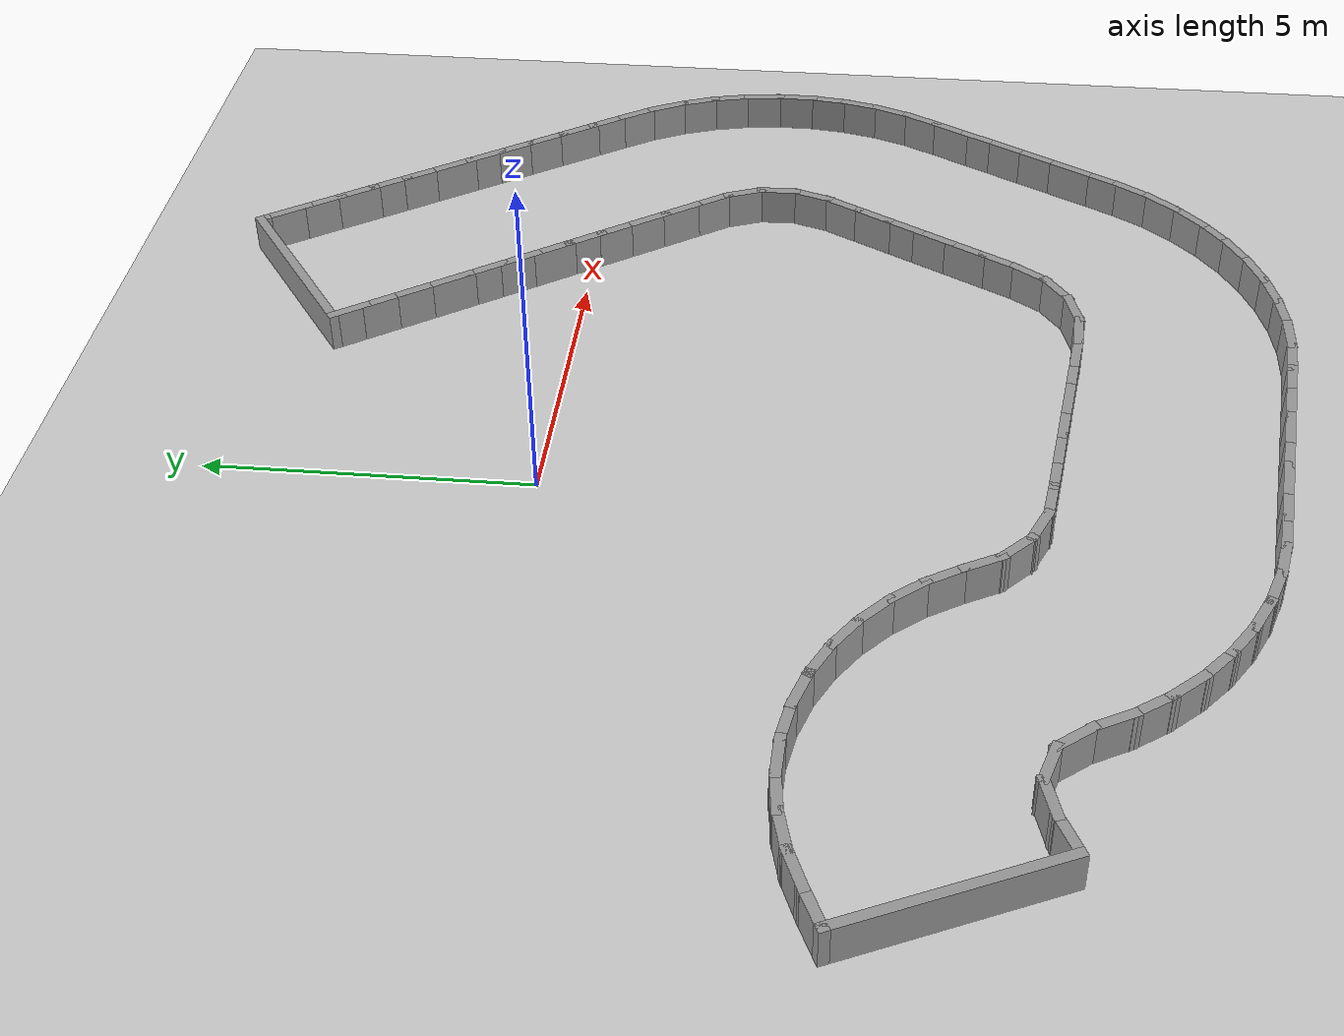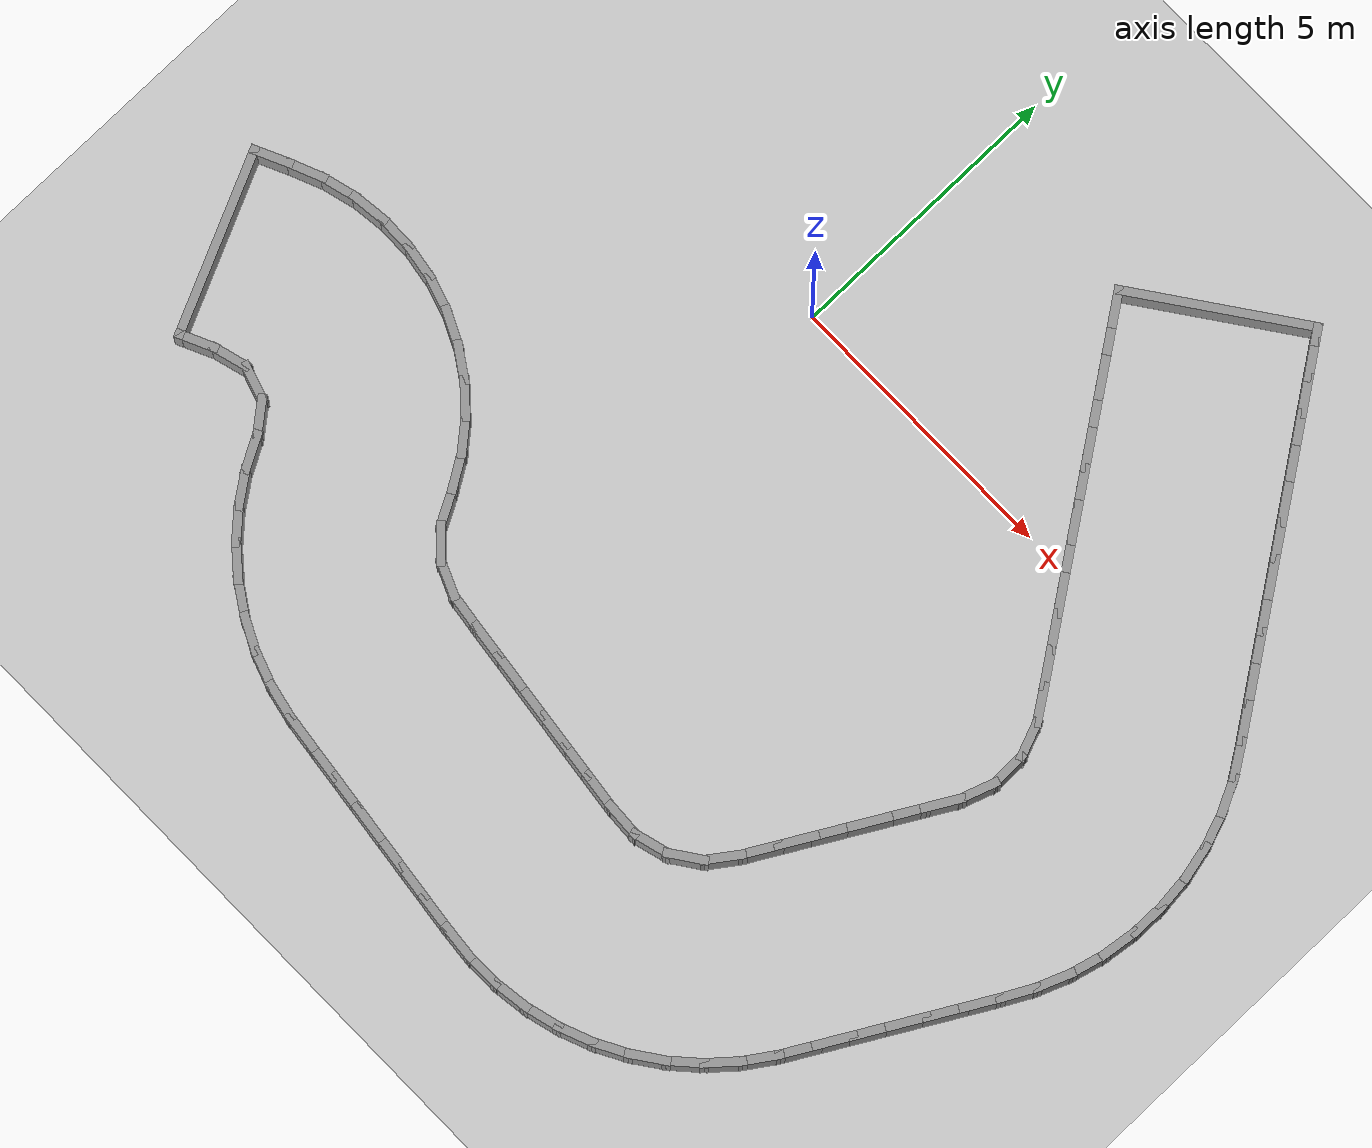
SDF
<?xml version="1.0" ?>
<sdf version='1.7'>
  <world name='default'>
    <plugin name='gazebo_ros_state' filename='libgazebo_ros_state.so'>
      <ros>
        <namespace>/</namespace>
      </ros>
      <update_rate>1000.0</update_rate>
    </plugin>

    <light name='sun' type='directional'>
      <cast_shadows>1</cast_shadows>
      <pose>0 0 10 0 -0 0</pose>
      <diffuse>0.8 0.8 0.8 1</diffuse>
      <specular>0.2 0.2 0.2 1</specular>
      <attenuation>
        <range>1000</range>
        <constant>0.9</constant>
        <linear>0.01</linear>
        <quadratic>0.001</quadratic>
      </attenuation>
      <direction>-0.5 0.1 -0.9</direction>
      <spot>
        <inner_angle>0</inner_angle>
        <outer_angle>0</outer_angle>
        <falloff>0</falloff>
      </spot>
    </light>
    <model name='ground_plane'>
      <static>1</static>
      <link name='link'>
        <collision name='collision'>
          <geometry>
            <plane>
              <normal>0 0 1</normal>
              <size>100 100</size>
            </plane>
          </geometry>
          <surface>
            <friction>
              <ode>
                <mu>100</mu>
                <mu2>50</mu2>
              </ode>
              <torsional>
                <ode/>
              </torsional>
            </friction>
            <contact>
              <ode/>
            </contact>
            <bounce/>
          </surface>
          <max_contacts>10</max_contacts>
        </collision>
        <visual name='visual'>
          <cast_shadows>0</cast_shadows>
          <geometry>
            <plane>
              <normal>0 0 1</normal>
              <size>100 100</size>
            </plane>
          </geometry>
          <material>
            <script>
              <uri>file://media/materials/scripts/gazebo.material</uri>
              <name>Gazebo/Grey</name>
            </script>
          </material>
        </visual>
        <self_collide>0</self_collide>
        <enable_wind>0</enable_wind>
        <kinematic>0</kinematic>
      </link>
    </model>
    <gravity>0 0 -9.8</gravity>
    <magnetic_field>6e-06 2.3e-05 -4.2e-05</magnetic_field>
    <atmosphere type='adiabatic'/>
    <physics type='ode'>
      <max_step_size>0.001</max_step_size>
      <real_time_factor>1</real_time_factor>
      <real_time_update_rate>1000</real_time_update_rate>
    </physics>
    <scene>
      <ambient>0.4 0.4 0.4 1</ambient>
      <background>0.7 0.7 0.7 1</background>
      <shadows>1</shadows>
    </scene>
    <audio>
      <device>default</device>
    </audio>
    <wind/>
    <spherical_coordinates>
      <surface_model>EARTH_WGS84</surface_model>
      <latitude_deg>0</latitude_deg>
      <longitude_deg>0</longitude_deg>
      <elevation>0</elevation>
      <heading_deg>0</heading_deg>
    </spherical_coordinates>
  <model name='rand_turn_06'>
    <pose>0 0 0 0 -0 0</pose>
    <link name='Wall_0'>
      <collision name='Wall_0_Collision'>
        <geometry><box><size>0.7500 0.1500 0.6000</size></box></geometry>
        <pose>0 0 0.3000 0 -0 0</pose>
      </collision>
      <visual name='Wall_0_Visual'>
        <pose>0 0 0.3000 0 -0 0</pose>
        <geometry><box><size>0.7500 0.1500 0.6000</size></box></geometry>
        <material>
          <script>
            <uri>file://media/materials/scripts/gazebo.material</uri>
            <name>Gazebo/Grey</name>
          </script>
          <ambient>1 1 1 1</ambient>
        </material>
      </visual>
      <pose>-7.8508 -4.4987 0 0 -0 0.43278</pose>
    </link>
    <link name='Wall_1'>
      <collision name='Wall_1_Collision'>
        <geometry><box><size>0.7496 0.1500 0.6000</size></box></geometry>
        <pose>0 0 0.3000 0 -0 0</pose>
      </collision>
      <visual name='Wall_1_Visual'>
        <pose>0 0 0.3000 0 -0 0</pose>
        <geometry><box><size>0.7496 0.1500 0.6000</size></box></geometry>
        <material>
          <script>
            <uri>file://media/materials/scripts/gazebo.material</uri>
            <name>Gazebo/Grey</name>
          </script>
          <ambient>1 1 1 1</ambient>
        </material>
      </visual>
      <pose>-7.3015 -4.2581 0 0 -0 0.39289</pose>
    </link>
    <link name='Wall_2'>
      <collision name='Wall_2_Collision'>
        <geometry><box><size>0.7495 0.1500 0.6000</size></box></geometry>
        <pose>0 0 0.3000 0 -0 0</pose>
      </collision>
      <visual name='Wall_2_Visual'>
        <pose>0 0 0.3000 0 -0 0</pose>
        <geometry><box><size>0.7495 0.1500 0.6000</size></box></geometry>
        <material>
          <script>
            <uri>file://media/materials/scripts/gazebo.material</uri>
            <name>Gazebo/Grey</name>
          </script>
          <ambient>1 1 1 1</ambient>
        </material>
      </visual>
      <pose>-6.7347 -4.0669 0 0 -0 0.25763</pose>
    </link>
    <link name='Wall_3'>
      <collision name='Wall_3_Collision'>
        <geometry><box><size>0.7495 0.1500 0.6000</size></box></geometry>
        <pose>0 0 0.3000 0 -0 0</pose>
      </collision>
      <visual name='Wall_3_Visual'>
        <pose>0 0 0.3000 0 -0 0</pose>
        <geometry><box><size>0.7495 0.1500 0.6000</size></box></geometry>
        <material>
          <script>
            <uri>file://media/materials/scripts/gazebo.material</uri>
            <name>Gazebo/Grey</name>
          </script>
          <ambient>1 1 1 1</ambient>
        </material>
      </visual>
      <pose>-6.1471 -3.9563 0 0 -0 0.11463</pose>
    </link>
    <link name='Wall_4'>
      <collision name='Wall_4_Collision'>
        <geometry><box><size>0.7494 0.1500 0.6000</size></box></geometry>
        <pose>0 0 0.3000 0 -0 0</pose>
      </collision>
      <visual name='Wall_4_Visual'>
        <pose>0 0 0.3000 0 -0 0</pose>
        <geometry><box><size>0.7494 0.1500 0.6000</size></box></geometry>
        <material>
          <script>
            <uri>file://media/materials/scripts/gazebo.material</uri>
            <name>Gazebo/Grey</name>
          </script>
          <ambient>1 1 1 1</ambient>
        </material>
      </visual>
      <pose>-5.5497 -3.9296 0 0 -0 -0.02550</pose>
    </link>
    <link name='Wall_5'>
      <collision name='Wall_5_Collision'>
        <geometry><box><size>0.7495 0.1500 0.6000</size></box></geometry>
        <pose>0 0 0.3000 0 -0 0</pose>
      </collision>
      <visual name='Wall_5_Visual'>
        <pose>0 0 0.3000 0 -0 0</pose>
        <geometry><box><size>0.7495 0.1500 0.6000</size></box></geometry>
        <material>
          <script>
            <uri>file://media/materials/scripts/gazebo.material</uri>
            <name>Gazebo/Grey</name>
          </script>
          <ambient>1 1 1 1</ambient>
        </material>
      </visual>
      <pose>-4.9544 -3.9867 0 0 -0 -0.16562</pose>
    </link>
    <link name='Wall_6'>
      <collision name='Wall_6_Collision'>
        <geometry><box><size>0.7495 0.1500 0.6000</size></box></geometry>
        <pose>0 0 0.3000 0 -0 0</pose>
      </collision>
      <visual name='Wall_6_Visual'>
        <pose>0 0 0.3000 0 -0 0</pose>
        <geometry><box><size>0.7495 0.1500 0.6000</size></box></geometry>
        <material>
          <script>
            <uri>file://media/materials/scripts/gazebo.material</uri>
            <name>Gazebo/Grey</name>
          </script>
          <ambient>1 1 1 1</ambient>
        </material>
      </visual>
      <pose>-4.3731 -4.1267 0 0 -0 -0.30713</pose>
    </link>
    <link name='Wall_7'>
      <collision name='Wall_7_Collision'>
        <geometry><box><size>0.7495 0.1500 0.6000</size></box></geometry>
        <pose>0 0 0.3000 0 -0 0</pose>
      </collision>
      <visual name='Wall_7_Visual'>
        <pose>0 0 0.3000 0 -0 0</pose>
        <geometry><box><size>0.7495 0.1500 0.6000</size></box></geometry>
        <material>
          <script>
            <uri>file://media/materials/scripts/gazebo.material</uri>
            <name>Gazebo/Grey</name>
          </script>
          <ambient>1 1 1 1</ambient>
        </material>
      </visual>
      <pose>-3.8173 -4.3474 0 0 -0 -0.44875</pose>
    </link>
    <link name='Wall_8'>
      <collision name='Wall_8_Collision'>
        <geometry><box><size>0.7494 0.1500 0.6000</size></box></geometry>
        <pose>0 0 0.3000 0 -0 0</pose>
      </collision>
      <visual name='Wall_8_Visual'>
        <pose>0 0 0.3000 0 -0 0</pose>
        <geometry><box><size>0.7494 0.1500 0.6000</size></box></geometry>
        <material>
          <script>
            <uri>file://media/materials/scripts/gazebo.material</uri>
            <name>Gazebo/Grey</name>
          </script>
          <ambient>1 1 1 1</ambient>
        </material>
      </visual>
      <pose>-3.2980 -4.6439 0 0 -0 -0.58887</pose>
    </link>
    <link name='Wall_9'>
      <collision name='Wall_9_Collision'>
        <geometry><box><size>0.7495 0.1500 0.6000</size></box></geometry>
        <pose>0 0 0.3000 0 -0 0</pose>
      </collision>
      <visual name='Wall_9_Visual'>
        <pose>0 0 0.3000 0 -0 0</pose>
        <geometry><box><size>0.7495 0.1500 0.6000</size></box></geometry>
        <material>
          <script>
            <uri>file://media/materials/scripts/gazebo.material</uri>
            <name>Gazebo/Grey</name>
          </script>
          <ambient>1 1 1 1</ambient>
        </material>
      </visual>
      <pose>-2.8252 -5.0100 0 0 -0 -0.72898</pose>
    </link>
    <link name='Wall_10'>
      <collision name='Wall_10_Collision'>
        <geometry><box><size>0.7495 0.1500 0.6000</size></box></geometry>
        <pose>0 0 0.3000 0 -0 0</pose>
      </collision>
      <visual name='Wall_10_Visual'>
        <pose>0 0 0.3000 0 -0 0</pose>
        <geometry><box><size>0.7495 0.1500 0.6000</size></box></geometry>
        <material>
          <script>
            <uri>file://media/materials/scripts/gazebo.material</uri>
            <name>Gazebo/Grey</name>
          </script>
          <ambient>1 1 1 1</ambient>
        </material>
      </visual>
      <pose>-2.4088 -5.4391 0 0 -0 -0.87191</pose>
    </link>
    <link name='Wall_11'>
      <collision name='Wall_11_Collision'>
        <geometry><box><size>0.7494 0.1500 0.6000</size></box></geometry>
        <pose>0 0 0.3000 0 -0 0</pose>
      </collision>
      <visual name='Wall_11_Visual'>
        <pose>0 0 0.3000 0 -0 0</pose>
        <geometry><box><size>0.7494 0.1500 0.6000</size></box></geometry>
        <material>
          <script>
            <uri>file://media/materials/scripts/gazebo.material</uri>
            <name>Gazebo/Grey</name>
          </script>
          <ambient>1 1 1 1</ambient>
        </material>
      </visual>
      <pose>-2.0571 -5.9228 0 0 -0 -1.01212</pose>
    </link>
    <link name='Wall_12'>
      <collision name='Wall_12_Collision'>
        <geometry><box><size>0.7490 0.1500 0.6000</size></box></geometry>
        <pose>0 0 0.3000 0 -0 0</pose>
      </collision>
      <visual name='Wall_12_Visual'>
        <pose>0 0 0.3000 0 -0 0</pose>
        <geometry><box><size>0.7490 0.1500 0.6000</size></box></geometry>
        <material>
          <script>
            <uri>file://media/materials/scripts/gazebo.material</uri>
            <name>Gazebo/Grey</name>
          </script>
          <ambient>1 1 1 1</ambient>
        </material>
      </visual>
      <pose>-1.7540 -6.4394 0 0 -0 -1.06830</pose>
    </link>
    <link name='Wall_13'>
      <collision name='Wall_13_Collision'>
        <geometry><box><size>0.7468 0.1500 0.6000</size></box></geometry>
        <pose>0 0 0.3000 0 -0 0</pose>
      </collision>
      <visual name='Wall_13_Visual'>
        <pose>0 0 0.3000 0 -0 0</pose>
        <geometry><box><size>0.7468 0.1500 0.6000</size></box></geometry>
        <material>
          <script>
            <uri>file://media/materials/scripts/gazebo.material</uri>
            <name>Gazebo/Grey</name>
          </script>
          <ambient>1 1 1 1</ambient>
        </material>
      </visual>
      <pose>-1.3932 -6.9072 0 0 -0 -0.75874</pose>
    </link>
    <link name='Wall_14'>
      <collision name='Wall_14_Collision'>
        <geometry><box><size>0.7468 0.1500 0.6000</size></box></geometry>
        <pose>0 0 0.3000 0 -0 0</pose>
      </collision>
      <visual name='Wall_14_Visual'>
        <pose>0 0 0.3000 0 -0 0</pose>
        <geometry><box><size>0.7468 0.1500 0.6000</size></box></geometry>
        <material>
          <script>
            <uri>file://media/materials/scripts/gazebo.material</uri>
            <name>Gazebo/Grey</name>
          </script>
          <ambient>1 1 1 1</ambient>
        </material>
      </visual>
      <pose>-0.9022 -7.2298 0 0 -0 -0.40408</pose>
    </link>
    <link name='Wall_15'>
      <collision name='Wall_15_Collision'>
        <geometry><box><size>0.7498 0.1500 0.6000</size></box></geometry>
        <pose>0 0 0.3000 0 -0 0</pose>
      </collision>
      <visual name='Wall_15_Visual'>
        <pose>0 0 0.3000 0 -0 0</pose>
        <geometry><box><size>0.7498 0.1500 0.6000</size></box></geometry>
        <material>
          <script>
            <uri>file://media/materials/scripts/gazebo.material</uri>
            <name>Gazebo/Grey</name>
          </script>
          <ambient>1 1 1 1</ambient>
        </material>
      </visual>
      <pose>-0.3310 -7.3898 0 0 -0 -0.14270</pose>
    </link>
    <link name='Wall_16'>
      <collision name='Wall_16_Collision'>
        <geometry><box><size>0.7500 0.1500 0.6000</size></box></geometry>
        <pose>0 0 0.3000 0 -0 0</pose>
      </collision>
      <visual name='Wall_16_Visual'>
        <pose>0 0 0.3000 0 -0 0</pose>
        <geometry><box><size>0.7500 0.1500 0.6000</size></box></geometry>
        <material>
          <script>
            <uri>file://media/materials/scripts/gazebo.material</uri>
            <name>Gazebo/Grey</name>
          </script>
          <ambient>1 1 1 1</ambient>
        </material>
      </visual>
      <pose>0.2633 -7.4713 0 0 -0 -0.12992</pose>
    </link>
    <link name='Wall_17'>
      <collision name='Wall_17_Collision'>
        <geometry><box><size>0.7500 0.1500 0.6000</size></box></geometry>
        <pose>0 0 0.3000 0 -0 0</pose>
      </collision>
      <visual name='Wall_17_Visual'>
        <pose>0 0 0.3000 0 -0 0</pose>
        <geometry><box><size>0.7500 0.1500 0.6000</size></box></geometry>
        <material>
          <script>
            <uri>file://media/materials/scripts/gazebo.material</uri>
            <name>Gazebo/Grey</name>
          </script>
          <ambient>1 1 1 1</ambient>
        </material>
      </visual>
      <pose>0.8583 -7.5490 0 0 -0 -0.12992</pose>
    </link>
    <link name='Wall_18'>
      <collision name='Wall_18_Collision'>
        <geometry><box><size>0.7500 0.1500 0.6000</size></box></geometry>
        <pose>0 0 0.3000 0 -0 0</pose>
      </collision>
      <visual name='Wall_18_Visual'>
        <pose>0 0 0.3000 0 -0 0</pose>
        <geometry><box><size>0.7500 0.1500 0.6000</size></box></geometry>
        <material>
          <script>
            <uri>file://media/materials/scripts/gazebo.material</uri>
            <name>Gazebo/Grey</name>
          </script>
          <ambient>1 1 1 1</ambient>
        </material>
      </visual>
      <pose>1.4532 -7.6268 0 0 -0 -0.12992</pose>
    </link>
    <link name='Wall_19'>
      <collision name='Wall_19_Collision'>
        <geometry><box><size>0.7500 0.1500 0.6000</size></box></geometry>
        <pose>0 0 0.3000 0 -0 0</pose>
      </collision>
      <visual name='Wall_19_Visual'>
        <pose>0 0 0.3000 0 -0 0</pose>
        <geometry><box><size>0.7500 0.1500 0.6000</size></box></geometry>
        <material>
          <script>
            <uri>file://media/materials/scripts/gazebo.material</uri>
            <name>Gazebo/Grey</name>
          </script>
          <ambient>1 1 1 1</ambient>
        </material>
      </visual>
      <pose>2.0481 -7.7045 0 0 -0 -0.12992</pose>
    </link>
    <link name='Wall_20'>
      <collision name='Wall_20_Collision'>
        <geometry><box><size>0.7500 0.1500 0.6000</size></box></geometry>
        <pose>0 0 0.3000 0 -0 0</pose>
      </collision>
      <visual name='Wall_20_Visual'>
        <pose>0 0 0.3000 0 -0 0</pose>
        <geometry><box><size>0.7500 0.1500 0.6000</size></box></geometry>
        <material>
          <script>
            <uri>file://media/materials/scripts/gazebo.material</uri>
            <name>Gazebo/Grey</name>
          </script>
          <ambient>1 1 1 1</ambient>
        </material>
      </visual>
      <pose>2.6431 -7.7822 0 0 -0 -0.12992</pose>
    </link>
    <link name='Wall_21'>
      <collision name='Wall_21_Collision'>
        <geometry><box><size>0.7500 0.1500 0.6000</size></box></geometry>
        <pose>0 0 0.3000 0 -0 0</pose>
      </collision>
      <visual name='Wall_21_Visual'>
        <pose>0 0 0.3000 0 -0 0</pose>
        <geometry><box><size>0.7500 0.1500 0.6000</size></box></geometry>
        <material>
          <script>
            <uri>file://media/materials/scripts/gazebo.material</uri>
            <name>Gazebo/Grey</name>
          </script>
          <ambient>1 1 1 1</ambient>
        </material>
      </visual>
      <pose>3.2380 -7.8600 0 0 -0 -0.12992</pose>
    </link>
    <link name='Wall_22'>
      <collision name='Wall_22_Collision'>
        <geometry><box><size>0.7483 0.1500 0.6000</size></box></geometry>
        <pose>0 0 0.3000 0 -0 0</pose>
      </collision>
      <visual name='Wall_22_Visual'>
        <pose>0 0 0.3000 0 -0 0</pose>
        <geometry><box><size>0.7483 0.1500 0.6000</size></box></geometry>
        <material>
          <script>
            <uri>file://media/materials/scripts/gazebo.material</uri>
            <name>Gazebo/Grey</name>
          </script>
          <ambient>1 1 1 1</ambient>
        </material>
      </visual>
      <pose>3.8342 -7.9160 0 0 -0 -0.05757</pose>
    </link>
    <link name='Wall_23'>
      <collision name='Wall_23_Collision'>
        <geometry><box><size>0.7470 0.1500 0.6000</size></box></geometry>
        <pose>0 0 0.3000 0 -0 0</pose>
      </collision>
      <visual name='Wall_23_Visual'>
        <pose>0 0 0.3000 0 -0 0</pose>
        <geometry><box><size>0.7470 0.1500 0.6000</size></box></geometry>
        <material>
          <script>
            <uri>file://media/materials/scripts/gazebo.material</uri>
            <name>Gazebo/Grey</name>
          </script>
          <ambient>1 1 1 1</ambient>
        </material>
      </visual>
      <pose>4.4209 -7.8551 0 0 -0 0.26481</pose>
    </link>
    <link name='Wall_24'>
      <collision name='Wall_24_Collision'>
        <geometry><box><size>0.7470 0.1500 0.6000</size></box></geometry>
        <pose>0 0 0.3000 0 -0 0</pose>
      </collision>
      <visual name='Wall_24_Visual'>
        <pose>0 0 0.3000 0 -0 0</pose>
        <geometry><box><size>0.7470 0.1500 0.6000</size></box></geometry>
        <material>
          <script>
            <uri>file://media/materials/scripts/gazebo.material</uri>
            <name>Gazebo/Grey</name>
          </script>
          <ambient>1 1 1 1</ambient>
        </material>
      </visual>
      <pose>4.9538 -7.6061 0 0 -0 0.60958</pose>
    </link>
    <link name='Wall_25'>
      <collision name='Wall_25_Collision'>
        <geometry><box><size>0.7475 0.1500 0.6000</size></box></geometry>
        <pose>0 0 0.3000 0 -0 0</pose>
      </collision>
      <visual name='Wall_25_Visual'>
        <pose>0 0 0.3000 0 -0 0</pose>
        <geometry><box><size>0.7475 0.1500 0.6000</size></box></geometry>
        <material>
          <script>
            <uri>file://media/materials/scripts/gazebo.material</uri>
            <name>Gazebo/Grey</name>
          </script>
          <ambient>1 1 1 1</ambient>
        </material>
      </visual>
      <pose>5.3727 -7.1925 0 0 -0 0.94822</pose>
    </link>
    <link name='Wall_26'>
      <collision name='Wall_26_Collision'>
        <geometry><box><size>0.7500 0.1500 0.6000</size></box></geometry>
        <pose>0 0 0.3000 0 -0 0</pose>
      </collision>
      <visual name='Wall_26_Visual'>
        <pose>0 0 0.3000 0 -0 0</pose>
        <geometry><box><size>0.7500 0.1500 0.6000</size></box></geometry>
        <material>
          <script>
            <uri>file://media/materials/scripts/gazebo.material</uri>
            <name>Gazebo/Grey</name>
          </script>
          <ambient>1 1 1 1</ambient>
        </material>
      </visual>
      <pose>5.6947 -6.6888 0 0 -0 1.05565</pose>
    </link>
    <link name='Wall_27'>
      <collision name='Wall_27_Collision'>
        <geometry><box><size>0.7500 0.1500 0.6000</size></box></geometry>
        <pose>0 0 0.3000 0 -0 0</pose>
      </collision>
      <visual name='Wall_27_Visual'>
        <pose>0 0 0.3000 0 -0 0</pose>
        <geometry><box><size>0.7500 0.1500 0.6000</size></box></geometry>
        <material>
          <script>
            <uri>file://media/materials/scripts/gazebo.material</uri>
            <name>Gazebo/Grey</name>
          </script>
          <ambient>1 1 1 1</ambient>
        </material>
      </visual>
      <pose>5.9903 -6.1666 0 0 -0 1.05565</pose>
    </link>
    <link name='Wall_28'>
      <collision name='Wall_28_Collision'>
        <geometry><box><size>0.7500 0.1500 0.6000</size></box></geometry>
        <pose>0 0 0.3000 0 -0 0</pose>
      </collision>
      <visual name='Wall_28_Visual'>
        <pose>0 0 0.3000 0 -0 0</pose>
        <geometry><box><size>0.7500 0.1500 0.6000</size></box></geometry>
        <material>
          <script>
            <uri>file://media/materials/scripts/gazebo.material</uri>
            <name>Gazebo/Grey</name>
          </script>
          <ambient>1 1 1 1</ambient>
        </material>
      </visual>
      <pose>6.2859 -5.6445 0 0 -0 1.05565</pose>
    </link>
    <link name='Wall_29'>
      <collision name='Wall_29_Collision'>
        <geometry><box><size>0.7500 0.1500 0.6000</size></box></geometry>
        <pose>0 0 0.3000 0 -0 0</pose>
      </collision>
      <visual name='Wall_29_Visual'>
        <pose>0 0 0.3000 0 -0 0</pose>
        <geometry><box><size>0.7500 0.1500 0.6000</size></box></geometry>
        <material>
          <script>
            <uri>file://media/materials/scripts/gazebo.material</uri>
            <name>Gazebo/Grey</name>
          </script>
          <ambient>1 1 1 1</ambient>
        </material>
      </visual>
      <pose>6.5815 -5.1224 0 0 -0 1.05565</pose>
    </link>
    <link name='Wall_30'>
      <collision name='Wall_30_Collision'>
        <geometry><box><size>0.7500 0.1500 0.6000</size></box></geometry>
        <pose>0 0 0.3000 0 -0 0</pose>
      </collision>
      <visual name='Wall_30_Visual'>
        <pose>0 0 0.3000 0 -0 0</pose>
        <geometry><box><size>0.7500 0.1500 0.6000</size></box></geometry>
        <material>
          <script>
            <uri>file://media/materials/scripts/gazebo.material</uri>
            <name>Gazebo/Grey</name>
          </script>
          <ambient>1 1 1 1</ambient>
        </material>
      </visual>
      <pose>6.8771 -4.6002 0 0 -0 1.05565</pose>
    </link>
    <link name='Wall_31'>
      <collision name='Wall_31_Collision'>
        <geometry><box><size>0.7500 0.1500 0.6000</size></box></geometry>
        <pose>0 0 0.3000 0 -0 0</pose>
      </collision>
      <visual name='Wall_31_Visual'>
        <pose>0 0 0.3000 0 -0 0</pose>
        <geometry><box><size>0.7500 0.1500 0.6000</size></box></geometry>
        <material>
          <script>
            <uri>file://media/materials/scripts/gazebo.material</uri>
            <name>Gazebo/Grey</name>
          </script>
          <ambient>1 1 1 1</ambient>
        </material>
      </visual>
      <pose>7.1726 -4.0780 0 0 -0 1.05606</pose>
    </link>
    <link name='Wall_32'>
      <collision name='Wall_32_Collision'>
        <geometry><box><size>0.7469 0.1500 0.6000</size></box></geometry>
        <pose>0 0 0.3000 0 -0 0</pose>
      </collision>
      <visual name='Wall_32_Visual'>
        <pose>0 0 0.3000 0 -0 0</pose>
        <geometry><box><size>0.7469 0.1500 0.6000</size></box></geometry>
        <material>
          <script>
            <uri>file://media/materials/scripts/gazebo.material</uri>
            <name>Gazebo/Grey</name>
          </script>
          <ambient>1 1 1 1</ambient>
        </material>
      </visual>
      <pose>7.4179 -3.5349 0 0 -0 1.23779</pose>
    </link>
    <link name='Wall_33'>
      <collision name='Wall_33_Collision'>
        <geometry><box><size>0.7469 0.1500 0.6000</size></box></geometry>
        <pose>0 0 0.3000 0 -0 0</pose>
      </collision>
      <visual name='Wall_33_Visual'>
        <pose>0 0 0.3000 0 -0 0</pose>
        <geometry><box><size>0.7469 0.1500 0.6000</size></box></geometry>
        <material>
          <script>
            <uri>file://media/materials/scripts/gazebo.material</uri>
            <name>Gazebo/Grey</name>
          </script>
          <ambient>1 1 1 1</ambient>
        </material>
      </visual>
      <pose>7.5094 -2.9545 0 0 -0 1.59085</pose>
    </link>
    <link name='Wall_34'>
      <collision name='Wall_34_Collision'>
        <geometry><box><size>0.7469 0.1500 0.6000</size></box></geometry>
        <pose>0 0 0.3000 0 -0 0</pose>
      </collision>
      <visual name='Wall_34_Visual'>
        <pose>0 0 0.3000 0 -0 0</pose>
        <geometry><box><size>0.7469 0.1500 0.6000</size></box></geometry>
        <material>
          <script>
            <uri>file://media/materials/scripts/gazebo.material</uri>
            <name>Gazebo/Grey</name>
          </script>
          <ambient>1 1 1 1</ambient>
        </material>
      </visual>
      <pose>7.3949 -2.3781 0 0 -0 1.94325</pose>
    </link>
    <link name='Wall_35'>
      <collision name='Wall_35_Collision'>
        <geometry><box><size>0.7499 0.1500 0.6000</size></box></geometry>
        <pose>0 0 0.3000 0 -0 0</pose>
      </collision>
      <visual name='Wall_35_Visual'>
        <pose>0 0 0.3000 0 -0 0</pose>
        <geometry><box><size>0.7499 0.1500 0.6000</size></box></geometry>
        <material>
          <script>
            <uri>file://media/materials/scripts/gazebo.material</uri>
            <name>Gazebo/Grey</name>
          </script>
          <ambient>1 1 1 1</ambient>
        </material>
      </visual>
      <pose>7.1149 -1.8540 0 0 -0 2.17899</pose>
    </link>
    <link name='Wall_36'>
      <collision name='Wall_36_Collision'>
        <geometry><box><size>0.7500 0.1500 0.6000</size></box></geometry>
        <pose>0 0 0.3000 0 -0 0</pose>
      </collision>
      <visual name='Wall_36_Visual'>
        <pose>0 0 0.3000 0 -0 0</pose>
        <geometry><box><size>0.7500 0.1500 0.6000</size></box></geometry>
        <material>
          <script>
            <uri>file://media/materials/scripts/gazebo.material</uri>
            <name>Gazebo/Grey</name>
          </script>
          <ambient>1 1 1 1</ambient>
        </material>
      </visual>
      <pose>6.7707 -1.3626 0 0 -0 2.18462</pose>
    </link>
    <link name='Wall_37'>
      <collision name='Wall_37_Collision'>
        <geometry><box><size>0.7500 0.1500 0.6000</size></box></geometry>
        <pose>0 0 0.3000 0 -0 0</pose>
      </collision>
      <visual name='Wall_37_Visual'>
        <pose>0 0 0.3000 0 -0 0</pose>
        <geometry><box><size>0.7500 0.1500 0.6000</size></box></geometry>
        <material>
          <script>
            <uri>file://media/materials/scripts/gazebo.material</uri>
            <name>Gazebo/Grey</name>
          </script>
          <ambient>1 1 1 1</ambient>
        </material>
      </visual>
      <pose>6.4251 -0.8721 0 0 -0 2.18462</pose>
    </link>
    <link name='Wall_38'>
      <collision name='Wall_38_Collision'>
        <geometry><box><size>0.7500 0.1500 0.6000</size></box></geometry>
        <pose>0 0 0.3000 0 -0 0</pose>
      </collision>
      <visual name='Wall_38_Visual'>
        <pose>0 0 0.3000 0 -0 0</pose>
        <geometry><box><size>0.7500 0.1500 0.6000</size></box></geometry>
        <material>
          <script>
            <uri>file://media/materials/scripts/gazebo.material</uri>
            <name>Gazebo/Grey</name>
          </script>
          <ambient>1 1 1 1</ambient>
        </material>
      </visual>
      <pose>6.0795 -0.3816 0 0 -0 2.18462</pose>
    </link>
    <link name='Wall_39'>
      <collision name='Wall_39_Collision'>
        <geometry><box><size>0.7500 0.1500 0.6000</size></box></geometry>
        <pose>0 0 0.3000 0 -0 0</pose>
      </collision>
      <visual name='Wall_39_Visual'>
        <pose>0 0 0.3000 0 -0 0</pose>
        <geometry><box><size>0.7500 0.1500 0.6000</size></box></geometry>
        <material>
          <script>
            <uri>file://media/materials/scripts/gazebo.material</uri>
            <name>Gazebo/Grey</name>
          </script>
          <ambient>1 1 1 1</ambient>
        </material>
      </visual>
      <pose>5.7339 0.1089 0 0 -0 2.18462</pose>
    </link>
    <link name='Wall_40'>
      <collision name='Wall_40_Collision'>
        <geometry><box><size>0.7500 0.1500 0.6000</size></box></geometry>
        <pose>0 0 0.3000 0 -0 0</pose>
      </collision>
      <visual name='Wall_40_Visual'>
        <pose>0 0 0.3000 0 -0 0</pose>
        <geometry><box><size>0.7500 0.1500 0.6000</size></box></geometry>
        <material>
          <script>
            <uri>file://media/materials/scripts/gazebo.material</uri>
            <name>Gazebo/Grey</name>
          </script>
          <ambient>1 1 1 1</ambient>
        </material>
      </visual>
      <pose>5.3883 0.5993 0 0 -0 2.18462</pose>
    </link>
    <link name='Wall_41'>
      <collision name='Wall_41_Collision'>
        <geometry><box><size>0.7500 0.1500 0.6000</size></box></geometry>
        <pose>0 0 0.3000 0 -0 0</pose>
      </collision>
      <visual name='Wall_41_Visual'>
        <pose>0 0 0.3000 0 -0 0</pose>
        <geometry><box><size>0.7500 0.1500 0.6000</size></box></geometry>
        <material>
          <script>
            <uri>file://media/materials/scripts/gazebo.material</uri>
            <name>Gazebo/Grey</name>
          </script>
          <ambient>1 1 1 1</ambient>
        </material>
      </visual>
      <pose>5.0427 1.0898 0 0 -0 2.18462</pose>
    </link>
    <link name='Wall_42'>
      <collision name='Wall_42_Collision'>
        <geometry><box><size>0.7500 0.1500 0.6000</size></box></geometry>
        <pose>0 0 0.3000 0 -0 0</pose>
      </collision>
      <visual name='Wall_42_Visual'>
        <pose>0 0 0.3000 0 -0 0</pose>
        <geometry><box><size>0.7500 0.1500 0.6000</size></box></geometry>
        <material>
          <script>
            <uri>file://media/materials/scripts/gazebo.material</uri>
            <name>Gazebo/Grey</name>
          </script>
          <ambient>1 1 1 1</ambient>
        </material>
      </visual>
      <pose>4.6971 1.5803 0 0 -0 2.18462</pose>
    </link>
    <link name='Wall_43'>
      <collision name='Wall_43_Collision'>
        <geometry><box><size>0.7500 0.1500 0.6000</size></box></geometry>
        <pose>0 0 0.3000 0 -0 0</pose>
      </collision>
      <visual name='Wall_43_Visual'>
        <pose>0 0 0.3000 0 -0 0</pose>
        <geometry><box><size>0.7500 0.1500 0.6000</size></box></geometry>
        <material>
          <script>
            <uri>file://media/materials/scripts/gazebo.material</uri>
            <name>Gazebo/Grey</name>
          </script>
          <ambient>1 1 1 1</ambient>
        </material>
      </visual>
      <pose>4.3515 2.0707 0 0 -0 2.18462</pose>
    </link>
    <link name='Wall_44'>
      <collision name='Wall_44_Collision'>
        <geometry><box><size>0.7500 0.1500 0.6000</size></box></geometry>
        <pose>0 0 0.3000 0 -0 0</pose>
      </collision>
      <visual name='Wall_44_Visual'>
        <pose>0 0 0.3000 0 -0 0</pose>
        <geometry><box><size>0.7500 0.1500 0.6000</size></box></geometry>
        <material>
          <script>
            <uri>file://media/materials/scripts/gazebo.material</uri>
            <name>Gazebo/Grey</name>
          </script>
          <ambient>1 1 1 1</ambient>
        </material>
      </visual>
      <pose>4.0059 2.5612 0 0 -0 2.18462</pose>
    </link>
    <link name='Wall_45'>
      <collision name='Wall_45_Collision'>
        <geometry><box><size>0.7500 0.1500 0.6000</size></box></geometry>
        <pose>0 0 0.3000 0 -0 0</pose>
      </collision>
      <visual name='Wall_45_Visual'>
        <pose>0 0 0.3000 0 -0 0</pose>
        <geometry><box><size>0.7500 0.1500 0.6000</size></box></geometry>
        <material>
          <script>
            <uri>file://media/materials/scripts/gazebo.material</uri>
            <name>Gazebo/Grey</name>
          </script>
          <ambient>1 1 1 1</ambient>
        </material>
      </visual>
      <pose>3.6603 3.0517 0 0 -0 2.18462</pose>
    </link>
    <link name='Wall_46'>
      <collision name='Wall_46_Collision'>
        <geometry><box><size>0.7092 0.1500 0.6000</size></box></geometry>
        <pose>0 0 0.3000 0 -0 0</pose>
      </collision>
      <visual name='Wall_46_Visual'>
        <pose>0 0 0.3000 0 -0 0</pose>
        <geometry><box><size>0.7092 0.1500 0.6000</size></box></geometry>
        <material>
          <script>
            <uri>file://media/materials/scripts/gazebo.material</uri>
            <name>Gazebo/Grey</name>
          </script>
          <ambient>1 1 1 1</ambient>
        </material>
      </visual>
      <pose>3.3265 3.5255 0 0 -0 2.18462</pose>
    </link>
    <link name='Wall_47'>
      <collision name='Wall_47_Collision'>
        <geometry><box><size>0.7500 0.1500 0.6000</size></box></geometry>
        <pose>0 0 0.3000 0 -0 0</pose>
      </collision>
      <visual name='Wall_47_Visual'>
        <pose>0 0 0.3000 0 -0 0</pose>
        <geometry><box><size>0.7500 0.1500 0.6000</size></box></geometry>
        <material>
          <script>
            <uri>file://media/materials/scripts/gazebo.material</uri>
            <name>Gazebo/Grey</name>
          </script>
          <ambient>1 1 1 1</ambient>
        </material>
      </visual>
      <pose>-6.4909 -7.4423 0 0 -0 0.43278</pose>
    </link>
    <link name='Wall_48'>
      <collision name='Wall_48_Collision'>
        <geometry><box><size>0.7435 0.1500 0.6000</size></box></geometry>
        <pose>0 0 0.3000 0 -0 0</pose>
      </collision>
      <visual name='Wall_48_Visual'>
        <pose>0 0 0.3000 0 -0 0</pose>
        <geometry><box><size>0.7435 0.1500 0.6000</size></box></geometry>
        <material>
          <script>
            <uri>file://media/materials/scripts/gazebo.material</uri>
            <name>Gazebo/Grey</name>
          </script>
          <ambient>1 1 1 1</ambient>
        </material>
      </visual>
      <pose>-5.9324 -7.2381 0 0 -0 0.26725</pose>
    </link>
    <link name='Wall_49'>
      <collision name='Wall_49_Collision'>
        <geometry><box><size>0.7413 0.1500 0.6000</size></box></geometry>
        <pose>0 0 0.3000 0 -0 0</pose>
      </collision>
      <visual name='Wall_49_Visual'>
        <pose>0 0 0.3000 0 -0 0</pose>
        <geometry><box><size>0.7413 0.1500 0.6000</size></box></geometry>
        <material>
          <script>
            <uri>file://media/materials/scripts/gazebo.material</uri>
            <name>Gazebo/Grey</name>
          </script>
          <ambient>1 1 1 1</ambient>
        </material>
      </visual>
      <pose>-5.3643 -7.2489 0 0 -0 -0.30638</pose>
    </link>
    <link name='Wall_50'>
      <collision name='Wall_50_Collision'>
        <geometry><box><size>0.7418 0.1500 0.6000</size></box></geometry>
        <pose>0 0 0.3000 0 -0 0</pose>
      </collision>
      <visual name='Wall_50_Visual'>
        <pose>0 0 0.3000 0 -0 0</pose>
        <geometry><box><size>0.7418 0.1500 0.6000</size></box></geometry>
        <material>
          <script>
            <uri>file://media/materials/scripts/gazebo.material</uri>
            <name>Gazebo/Grey</name>
          </script>
          <ambient>1 1 1 1</ambient>
        </material>
      </visual>
      <pose>-4.8971 -7.5688 0 0 -0 -0.89418</pose>
    </link>
    <link name='Wall_51'>
      <collision name='Wall_51_Collision'>
        <geometry><box><size>0.7496 0.1500 0.6000</size></box></geometry>
        <pose>0 0 0.3000 0 -0 0</pose>
      </collision>
      <visual name='Wall_51_Visual'>
        <pose>0 0 0.3000 0 -0 0</pose>
        <geometry><box><size>0.7496 0.1500 0.6000</size></box></geometry>
        <material>
          <script>
            <uri>file://media/materials/scripts/gazebo.material</uri>
            <name>Gazebo/Grey</name>
          </script>
          <ambient>1 1 1 1</ambient>
        </material>
      </visual>
      <pose>-4.5679 -8.0625 0 0 -0 -1.07000</pose>
    </link>
    <link name='Wall_52'>
      <collision name='Wall_52_Collision'>
        <geometry><box><size>0.7496 0.1500 0.6000</size></box></geometry>
        <pose>0 0 0.3000 0 -0 0</pose>
      </collision>
      <visual name='Wall_52_Visual'>
        <pose>0 0 0.3000 0 -0 0</pose>
        <geometry><box><size>0.7496 0.1500 0.6000</size></box></geometry>
        <material>
          <script>
            <uri>file://media/materials/scripts/gazebo.material</uri>
            <name>Gazebo/Grey</name>
          </script>
          <ambient>1 1 1 1</ambient>
        </material>
      </visual>
      <pose>-4.2493 -8.5691 0 0 -0 -0.94862</pose>
    </link>
    <link name='Wall_53'>
      <collision name='Wall_53_Collision'>
        <geometry><box><size>0.7496 0.1500 0.6000</size></box></geometry>
        <pose>0 0 0.3000 0 -0 0</pose>
      </collision>
      <visual name='Wall_53_Visual'>
        <pose>0 0 0.3000 0 -0 0</pose>
        <geometry><box><size>0.7496 0.1500 0.6000</size></box></geometry>
        <material>
          <script>
            <uri>file://media/materials/scripts/gazebo.material</uri>
            <name>Gazebo/Grey</name>
          </script>
          <ambient>1 1 1 1</ambient>
        </material>
      </visual>
      <pose>-3.8716 -9.0333 0 0 -0 -0.82701</pose>
    </link>
    <link name='Wall_54'>
      <collision name='Wall_54_Collision'>
        <geometry><box><size>0.7496 0.1500 0.6000</size></box></geometry>
        <pose>0 0 0.3000 0 -0 0</pose>
      </collision>
      <visual name='Wall_54_Visual'>
        <pose>0 0 0.3000 0 -0 0</pose>
        <geometry><box><size>0.7496 0.1500 0.6000</size></box></geometry>
        <material>
          <script>
            <uri>file://media/materials/scripts/gazebo.material</uri>
            <name>Gazebo/Grey</name>
          </script>
          <ambient>1 1 1 1</ambient>
        </material>
      </visual>
      <pose>-3.4403 -9.4483 0 0 -0 -0.70540</pose>
    </link>
    <link name='Wall_55'>
      <collision name='Wall_55_Collision'>
        <geometry><box><size>0.7496 0.1500 0.6000</size></box></geometry>
        <pose>0 0 0.3000 0 -0 0</pose>
      </collision>
      <visual name='Wall_55_Visual'>
        <pose>0 0 0.3000 0 -0 0</pose>
        <geometry><box><size>0.7496 0.1500 0.6000</size></box></geometry>
        <material>
          <script>
            <uri>file://media/materials/scripts/gazebo.material</uri>
            <name>Gazebo/Grey</name>
          </script>
          <ambient>1 1 1 1</ambient>
        </material>
      </visual>
      <pose>-2.9619 -9.8079 0 0 -0 -0.58379</pose>
    </link>
    <link name='Wall_56'>
      <collision name='Wall_56_Collision'>
        <geometry><box><size>0.7496 0.1500 0.6000</size></box></geometry>
        <pose>0 0 0.3000 0 -0 0</pose>
      </collision>
      <visual name='Wall_56_Visual'>
        <pose>0 0 0.3000 0 -0 0</pose>
        <geometry><box><size>0.7496 0.1500 0.6000</size></box></geometry>
        <material>
          <script>
            <uri>file://media/materials/scripts/gazebo.material</uri>
            <name>Gazebo/Grey</name>
          </script>
          <ambient>1 1 1 1</ambient>
        </material>
      </visual>
      <pose>-2.4435 -10.1068 0 0 -0 -0.46217</pose>
    </link>
    <link name='Wall_57'>
      <collision name='Wall_57_Collision'>
        <geometry><box><size>0.7496 0.1500 0.6000</size></box></geometry>
        <pose>0 0 0.3000 0 -0 0</pose>
      </collision>
      <visual name='Wall_57_Visual'>
        <pose>0 0 0.3000 0 -0 0</pose>
        <geometry><box><size>0.7496 0.1500 0.6000</size></box></geometry>
        <material>
          <script>
            <uri>file://media/materials/scripts/gazebo.material</uri>
            <name>Gazebo/Grey</name>
          </script>
          <ambient>1 1 1 1</ambient>
        </material>
      </visual>
      <pose>-1.8925 -10.3407 0 0 -0 -0.34056</pose>
    </link>
    <link name='Wall_58'>
      <collision name='Wall_58_Collision'>
        <geometry><box><size>0.7496 0.1500 0.6000</size></box></geometry>
        <pose>0 0 0.3000 0 -0 0</pose>
      </collision>
      <visual name='Wall_58_Visual'>
        <pose>0 0 0.3000 0 -0 0</pose>
        <geometry><box><size>0.7496 0.1500 0.6000</size></box></geometry>
        <material>
          <script>
            <uri>file://media/materials/scripts/gazebo.material</uri>
            <name>Gazebo/Grey</name>
          </script>
          <ambient>1 1 1 1</ambient>
        </material>
      </visual>
      <pose>-1.3173 -10.5059 0 0 -0 -0.21894</pose>
    </link>
    <link name='Wall_59'>
      <collision name='Wall_59_Collision'>
        <geometry><box><size>0.7500 0.1500 0.6000</size></box></geometry>
        <pose>0 0 0.3000 0 -0 0</pose>
      </collision>
      <visual name='Wall_59_Visual'>
        <pose>0 0 0.3000 0 -0 0</pose>
        <geometry><box><size>0.7500 0.1500 0.6000</size></box></geometry>
        <material>
          <script>
            <uri>file://media/materials/scripts/gazebo.material</uri>
            <name>Gazebo/Grey</name>
          </script>
          <ambient>1 1 1 1</ambient>
        </material>
      </visual>
      <pose>-0.7274 -10.6109 0 0 -0 -0.13343</pose>
    </link>
    <link name='Wall_60'>
      <collision name='Wall_60_Collision'>
        <geometry><box><size>0.7500 0.1500 0.6000</size></box></geometry>
        <pose>0 0 0.3000 0 -0 0</pose>
      </collision>
      <visual name='Wall_60_Visual'>
        <pose>0 0 0.3000 0 -0 0</pose>
        <geometry><box><size>0.7500 0.1500 0.6000</size></box></geometry>
        <material>
          <script>
            <uri>file://media/materials/scripts/gazebo.material</uri>
            <name>Gazebo/Grey</name>
          </script>
          <ambient>1 1 1 1</ambient>
        </material>
      </visual>
      <pose>-0.1326 -10.6897 0 0 -0 -0.12992</pose>
    </link>
    <link name='Wall_61'>
      <collision name='Wall_61_Collision'>
        <geometry><box><size>0.7500 0.1500 0.6000</size></box></geometry>
        <pose>0 0 0.3000 0 -0 0</pose>
      </collision>
      <visual name='Wall_61_Visual'>
        <pose>0 0 0.3000 0 -0 0</pose>
        <geometry><box><size>0.7500 0.1500 0.6000</size></box></geometry>
        <material>
          <script>
            <uri>file://media/materials/scripts/gazebo.material</uri>
            <name>Gazebo/Grey</name>
          </script>
          <ambient>1 1 1 1</ambient>
        </material>
      </visual>
      <pose>0.4624 -10.7674 0 0 -0 -0.12992</pose>
    </link>
    <link name='Wall_62'>
      <collision name='Wall_62_Collision'>
        <geometry><box><size>0.7500 0.1500 0.6000</size></box></geometry>
        <pose>0 0 0.3000 0 -0 0</pose>
      </collision>
      <visual name='Wall_62_Visual'>
        <pose>0 0 0.3000 0 -0 0</pose>
        <geometry><box><size>0.7500 0.1500 0.6000</size></box></geometry>
        <material>
          <script>
            <uri>file://media/materials/scripts/gazebo.material</uri>
            <name>Gazebo/Grey</name>
          </script>
          <ambient>1 1 1 1</ambient>
        </material>
      </visual>
      <pose>1.0573 -10.8452 0 0 -0 -0.12992</pose>
    </link>
    <link name='Wall_63'>
      <collision name='Wall_63_Collision'>
        <geometry><box><size>0.7500 0.1500 0.6000</size></box></geometry>
        <pose>0 0 0.3000 0 -0 0</pose>
      </collision>
      <visual name='Wall_63_Visual'>
        <pose>0 0 0.3000 0 -0 0</pose>
        <geometry><box><size>0.7500 0.1500 0.6000</size></box></geometry>
        <material>
          <script>
            <uri>file://media/materials/scripts/gazebo.material</uri>
            <name>Gazebo/Grey</name>
          </script>
          <ambient>1 1 1 1</ambient>
        </material>
      </visual>
      <pose>1.6522 -10.9229 0 0 -0 -0.12992</pose>
    </link>
    <link name='Wall_64'>
      <collision name='Wall_64_Collision'>
        <geometry><box><size>0.7500 0.1500 0.6000</size></box></geometry>
        <pose>0 0 0.3000 0 -0 0</pose>
      </collision>
      <visual name='Wall_64_Visual'>
        <pose>0 0 0.3000 0 -0 0</pose>
        <geometry><box><size>0.7500 0.1500 0.6000</size></box></geometry>
        <material>
          <script>
            <uri>file://media/materials/scripts/gazebo.material</uri>
            <name>Gazebo/Grey</name>
          </script>
          <ambient>1 1 1 1</ambient>
        </material>
      </visual>
      <pose>2.2472 -11.0006 0 0 -0 -0.12992</pose>
    </link>
    <link name='Wall_65'>
      <collision name='Wall_65_Collision'>
        <geometry><box><size>0.7500 0.1500 0.6000</size></box></geometry>
        <pose>0 0 0.3000 0 -0 0</pose>
      </collision>
      <visual name='Wall_65_Visual'>
        <pose>0 0 0.3000 0 -0 0</pose>
        <geometry><box><size>0.7500 0.1500 0.6000</size></box></geometry>
        <material>
          <script>
            <uri>file://media/materials/scripts/gazebo.material</uri>
            <name>Gazebo/Grey</name>
          </script>
          <ambient>1 1 1 1</ambient>
        </material>
      </visual>
      <pose>2.8421 -11.0784 0 0 -0 -0.12992</pose>
    </link>
    <link name='Wall_66'>
      <collision name='Wall_66_Collision'>
        <geometry><box><size>0.7498 0.1500 0.6000</size></box></geometry>
        <pose>0 0 0.3000 0 -0 0</pose>
      </collision>
      <visual name='Wall_66_Visual'>
        <pose>0 0 0.3000 0 -0 0</pose>
        <geometry><box><size>0.7498 0.1500 0.6000</size></box></geometry>
        <material>
          <script>
            <uri>file://media/materials/scripts/gazebo.material</uri>
            <name>Gazebo/Grey</name>
          </script>
          <ambient>1 1 1 1</ambient>
        </material>
      </visual>
      <pose>3.4380 -11.1474 0 0 -0 -0.10084</pose>
    </link>
    <link name='Wall_67'>
      <collision name='Wall_67_Collision'>
        <geometry><box><size>0.7496 0.1500 0.6000</size></box></geometry>
        <pose>0 0 0.3000 0 -0 0</pose>
      </collision>
      <visual name='Wall_67_Visual'>
        <pose>0 0 0.3000 0 -0 0</pose>
        <geometry><box><size>0.7496 0.1500 0.6000</size></box></geometry>
        <material>
          <script>
            <uri>file://media/materials/scripts/gazebo.material</uri>
            <name>Gazebo/Grey</name>
          </script>
          <ambient>1 1 1 1</ambient>
        </material>
      </visual>
      <pose>4.0361 -11.1737 0 0 -0 0.01292</pose>
    </link>
    <link name='Wall_68'>
      <collision name='Wall_68_Collision'>
        <geometry><box><size>0.7496 0.1500 0.6000</size></box></geometry>
        <pose>0 0 0.3000 0 -0 0</pose>
      </collision>
      <visual name='Wall_68_Visual'>
        <pose>0 0 0.3000 0 -0 0</pose>
        <geometry><box><size>0.7496 0.1500 0.6000</size></box></geometry>
        <material>
          <script>
            <uri>file://media/materials/scripts/gazebo.material</uri>
            <name>Gazebo/Grey</name>
          </script>
          <ambient>1 1 1 1</ambient>
        </material>
      </visual>
      <pose>4.6331 -11.1300 0 0 -0 0.13327</pose>
    </link>
    <link name='Wall_69'>
      <collision name='Wall_69_Collision'>
        <geometry><box><size>0.7496 0.1500 0.6000</size></box></geometry>
        <pose>0 0 0.3000 0 -0 0</pose>
      </collision>
      <visual name='Wall_69_Visual'>
        <pose>0 0 0.3000 0 -0 0</pose>
        <geometry><box><size>0.7496 0.1500 0.6000</size></box></geometry>
        <material>
          <script>
            <uri>file://media/materials/scripts/gazebo.material</uri>
            <name>Gazebo/Grey</name>
          </script>
          <ambient>1 1 1 1</ambient>
        </material>
      </visual>
      <pose>5.2204 -11.0150 0 0 -0 0.25361</pose>
    </link>
    <link name='Wall_70'>
      <collision name='Wall_70_Collision'>
        <geometry><box><size>0.7496 0.1500 0.6000</size></box></geometry>
        <pose>0 0 0.3000 0 -0 0</pose>
      </collision>
      <visual name='Wall_70_Visual'>
        <pose>0 0 0.3000 0 -0 0</pose>
        <geometry><box><size>0.7496 0.1500 0.6000</size></box></geometry>
        <material>
          <script>
            <uri>file://media/materials/scripts/gazebo.material</uri>
            <name>Gazebo/Grey</name>
          </script>
          <ambient>1 1 1 1</ambient>
        </material>
      </visual>
      <pose>5.7898 -10.8302 0 0 -0 0.37396</pose>
    </link>
    <link name='Wall_71'>
      <collision name='Wall_71_Collision'>
        <geometry><box><size>0.7497 0.1500 0.6000</size></box></geometry>
        <pose>0 0 0.3000 0 -0 0</pose>
      </collision>
      <visual name='Wall_71_Visual'>
        <pose>0 0 0.3000 0 -0 0</pose>
        <geometry><box><size>0.7497 0.1500 0.6000</size></box></geometry>
        <material>
          <script>
            <uri>file://media/materials/scripts/gazebo.material</uri>
            <name>Gazebo/Grey</name>
          </script>
          <ambient>1 1 1 1</ambient>
        </material>
      </visual>
      <pose>6.3328 -10.5784 0 0 -0 0.49451</pose>
    </link>
    <link name='Wall_72'>
      <collision name='Wall_72_Collision'>
        <geometry><box><size>0.7496 0.1500 0.6000</size></box></geometry>
        <pose>0 0 0.3000 0 -0 0</pose>
      </collision>
      <visual name='Wall_72_Visual'>
        <pose>0 0 0.3000 0 -0 0</pose>
        <geometry><box><size>0.7496 0.1500 0.6000</size></box></geometry>
        <material>
          <script>
            <uri>file://media/materials/scripts/gazebo.material</uri>
            <name>Gazebo/Grey</name>
          </script>
          <ambient>1 1 1 1</ambient>
        </material>
      </visual>
      <pose>6.8416 -10.2631 0 0 -0 0.61501</pose>
    </link>
    <link name='Wall_73'>
      <collision name='Wall_73_Collision'>
        <geometry><box><size>0.7496 0.1500 0.6000</size></box></geometry>
        <pose>0 0 0.3000 0 -0 0</pose>
      </collision>
      <visual name='Wall_73_Visual'>
        <pose>0 0 0.3000 0 -0 0</pose>
        <geometry><box><size>0.7496 0.1500 0.6000</size></box></geometry>
        <material>
          <script>
            <uri>file://media/materials/scripts/gazebo.material</uri>
            <name>Gazebo/Grey</name>
          </script>
          <ambient>1 1 1 1</ambient>
        </material>
      </visual>
      <pose>7.3088 -9.8890 0 0 -0 0.73536</pose>
    </link>
    <link name='Wall_74'>
      <collision name='Wall_74_Collision'>
        <geometry><box><size>0.7496 0.1500 0.6000</size></box></geometry>
        <pose>0 0 0.3000 0 -0 0</pose>
      </collision>
      <visual name='Wall_74_Visual'>
        <pose>0 0 0.3000 0 -0 0</pose>
        <geometry><box><size>0.7496 0.1500 0.6000</size></box></geometry>
        <material>
          <script>
            <uri>file://media/materials/scripts/gazebo.material</uri>
            <name>Gazebo/Grey</name>
          </script>
          <ambient>1 1 1 1</ambient>
        </material>
      </visual>
      <pose>7.7277 -9.4615 0 0 -0 0.85570</pose>
    </link>
    <link name='Wall_75'>
      <collision name='Wall_75_Collision'>
        <geometry><box><size>0.7496 0.1500 0.6000</size></box></geometry>
        <pose>0 0 0.3000 0 -0 0</pose>
      </collision>
      <visual name='Wall_75_Visual'>
        <pose>0 0 0.3000 0 -0 0</pose>
        <geometry><box><size>0.7496 0.1500 0.6000</size></box></geometry>
        <material>
          <script>
            <uri>file://media/materials/scripts/gazebo.material</uri>
            <name>Gazebo/Grey</name>
          </script>
          <ambient>1 1 1 1</ambient>
        </material>
      </visual>
      <pose>8.0922 -8.9868 0 0 -0 0.97621</pose>
    </link>
    <link name='Wall_76'>
      <collision name='Wall_76_Collision'>
        <geometry><box><size>0.7500 0.1500 0.6000</size></box></geometry>
        <pose>0 0 0.3000 0 -0 0</pose>
      </collision>
      <visual name='Wall_76_Visual'>
        <pose>0 0 0.3000 0 -0 0</pose>
        <geometry><box><size>0.7500 0.1500 0.6000</size></box></geometry>
        <material>
          <script>
            <uri>file://media/materials/scripts/gazebo.material</uri>
            <name>Gazebo/Grey</name>
          </script>
          <ambient>1 1 1 1</ambient>
        </material>
      </visual>
      <pose>8.4081 -8.4774 0 0 -0 1.05518</pose>
    </link>
    <link name='Wall_77'>
      <collision name='Wall_77_Collision'>
        <geometry><box><size>0.7500 0.1500 0.6000</size></box></geometry>
        <pose>0 0 0.3000 0 -0 0</pose>
      </collision>
      <visual name='Wall_77_Visual'>
        <pose>0 0 0.3000 0 -0 0</pose>
        <geometry><box><size>0.7500 0.1500 0.6000</size></box></geometry>
        <material>
          <script>
            <uri>file://media/materials/scripts/gazebo.material</uri>
            <name>Gazebo/Grey</name>
          </script>
          <ambient>1 1 1 1</ambient>
        </material>
      </visual>
      <pose>8.7038 -7.9553 0 0 -0 1.05565</pose>
    </link>
    <link name='Wall_78'>
      <collision name='Wall_78_Collision'>
        <geometry><box><size>0.7500 0.1500 0.6000</size></box></geometry>
        <pose>0 0 0.3000 0 -0 0</pose>
      </collision>
      <visual name='Wall_78_Visual'>
        <pose>0 0 0.3000 0 -0 0</pose>
        <geometry><box><size>0.7500 0.1500 0.6000</size></box></geometry>
        <material>
          <script>
            <uri>file://media/materials/scripts/gazebo.material</uri>
            <name>Gazebo/Grey</name>
          </script>
          <ambient>1 1 1 1</ambient>
        </material>
      </visual>
      <pose>8.9994 -7.4332 0 0 -0 1.05565</pose>
    </link>
    <link name='Wall_79'>
      <collision name='Wall_79_Collision'>
        <geometry><box><size>0.7500 0.1500 0.6000</size></box></geometry>
        <pose>0 0 0.3000 0 -0 0</pose>
      </collision>
      <visual name='Wall_79_Visual'>
        <pose>0 0 0.3000 0 -0 0</pose>
        <geometry><box><size>0.7500 0.1500 0.6000</size></box></geometry>
        <material>
          <script>
            <uri>file://media/materials/scripts/gazebo.material</uri>
            <name>Gazebo/Grey</name>
          </script>
          <ambient>1 1 1 1</ambient>
        </material>
      </visual>
      <pose>9.2950 -6.9111 0 0 -0 1.05565</pose>
    </link>
    <link name='Wall_80'>
      <collision name='Wall_80_Collision'>
        <geometry><box><size>0.7500 0.1500 0.6000</size></box></geometry>
        <pose>0 0 0.3000 0 -0 0</pose>
      </collision>
      <visual name='Wall_80_Visual'>
        <pose>0 0 0.3000 0 -0 0</pose>
        <geometry><box><size>0.7500 0.1500 0.6000</size></box></geometry>
        <material>
          <script>
            <uri>file://media/materials/scripts/gazebo.material</uri>
            <name>Gazebo/Grey</name>
          </script>
          <ambient>1 1 1 1</ambient>
        </material>
      </visual>
      <pose>9.5906 -6.3890 0 0 -0 1.05565</pose>
    </link>
    <link name='Wall_81'>
      <collision name='Wall_81_Collision'>
        <geometry><box><size>0.7500 0.1500 0.6000</size></box></geometry>
        <pose>0 0 0.3000 0 -0 0</pose>
      </collision>
      <visual name='Wall_81_Visual'>
        <pose>0 0 0.3000 0 -0 0</pose>
        <geometry><box><size>0.7500 0.1500 0.6000</size></box></geometry>
        <material>
          <script>
            <uri>file://media/materials/scripts/gazebo.material</uri>
            <name>Gazebo/Grey</name>
          </script>
          <ambient>1 1 1 1</ambient>
        </material>
      </visual>
      <pose>9.8862 -5.8668 0 0 -0 1.05565</pose>
    </link>
    <link name='Wall_82'>
      <collision name='Wall_82_Collision'>
        <geometry><box><size>0.7498 0.1500 0.6000</size></box></geometry>
        <pose>0 0 0.3000 0 -0 0</pose>
      </collision>
      <visual name='Wall_82_Visual'>
        <pose>0 0 0.3000 0 -0 0</pose>
        <geometry><box><size>0.7498 0.1500 0.6000</size></box></geometry>
        <material>
          <script>
            <uri>file://media/materials/scripts/gazebo.material</uri>
            <name>Gazebo/Grey</name>
          </script>
          <ambient>1 1 1 1</ambient>
        </material>
      </visual>
      <pose>10.1748 -5.3409 0 0 -0 1.08224</pose>
    </link>
    <link name='Wall_83'>
      <collision name='Wall_83_Collision'>
        <geometry><box><size>0.7496 0.1500 0.6000</size></box></geometry>
        <pose>0 0 0.3000 0 -0 0</pose>
      </collision>
      <visual name='Wall_83_Visual'>
        <pose>0 0 0.3000 0 -0 0</pose>
        <geometry><box><size>0.7496 0.1500 0.6000</size></box></geometry>
        <material>
          <script>
            <uri>file://media/materials/scripts/gazebo.material</uri>
            <name>Gazebo/Grey</name>
          </script>
          <ambient>1 1 1 1</ambient>
        </material>
      </visual>
      <pose>10.4255 -4.7972 0 0 -0 1.19531</pose>
    </link>
    <link name='Wall_84'>
      <collision name='Wall_84_Collision'>
        <geometry><box><size>0.7496 0.1500 0.6000</size></box></geometry>
        <pose>0 0 0.3000 0 -0 0</pose>
      </collision>
      <visual name='Wall_84_Visual'>
        <pose>0 0 0.3000 0 -0 0</pose>
        <geometry><box><size>0.7496 0.1500 0.6000</size></box></geometry>
        <material>
          <script>
            <uri>file://media/materials/scripts/gazebo.material</uri>
            <name>Gazebo/Grey</name>
          </script>
          <ambient>1 1 1 1</ambient>
        </material>
      </visual>
      <pose>10.6108 -4.2282 0 0 -0 1.31666</pose>
    </link>
    <link name='Wall_85'>
      <collision name='Wall_85_Collision'>
        <geometry><box><size>0.7496 0.1500 0.6000</size></box></geometry>
        <pose>0 0 0.3000 0 -0 0</pose>
      </collision>
      <visual name='Wall_85_Visual'>
        <pose>0 0 0.3000 0 -0 0</pose>
        <geometry><box><size>0.7496 0.1500 0.6000</size></box></geometry>
        <material>
          <script>
            <uri>file://media/materials/scripts/gazebo.material</uri>
            <name>Gazebo/Grey</name>
          </script>
          <ambient>1 1 1 1</ambient>
        </material>
      </visual>
      <pose>10.7259 -3.6408 0 0 -0 1.43801</pose>
    </link>
    <link name='Wall_86'>
      <collision name='Wall_86_Collision'>
        <geometry><box><size>0.7496 0.1500 0.6000</size></box></geometry>
        <pose>0 0 0.3000 0 -0 0</pose>
      </collision>
      <visual name='Wall_86_Visual'>
        <pose>0 0 0.3000 0 -0 0</pose>
        <geometry><box><size>0.7496 0.1500 0.6000</size></box></geometry>
        <material>
          <script>
            <uri>file://media/materials/scripts/gazebo.material</uri>
            <name>Gazebo/Grey</name>
          </script>
          <ambient>1 1 1 1</ambient>
        </material>
      </visual>
      <pose>10.7690 -3.0439 0 0 -0 1.55935</pose>
    </link>
    <link name='Wall_87'>
      <collision name='Wall_87_Collision'>
        <geometry><box><size>0.7496 0.1500 0.6000</size></box></geometry>
        <pose>0 0 0.3000 0 -0 0</pose>
      </collision>
      <visual name='Wall_87_Visual'>
        <pose>0 0 0.3000 0 -0 0</pose>
        <geometry><box><size>0.7496 0.1500 0.6000</size></box></geometry>
        <material>
          <script>
            <uri>file://media/materials/scripts/gazebo.material</uri>
            <name>Gazebo/Grey</name>
          </script>
          <ambient>1 1 1 1</ambient>
        </material>
      </visual>
      <pose>10.7395 -2.4461 0 0 -0 1.68070</pose>
    </link>
    <link name='Wall_88'>
      <collision name='Wall_88_Collision'>
        <geometry><box><size>0.7496 0.1500 0.6000</size></box></geometry>
        <pose>0 0 0.3000 0 -0 0</pose>
      </collision>
      <visual name='Wall_88_Visual'>
        <pose>0 0 0.3000 0 -0 0</pose>
        <geometry><box><size>0.7496 0.1500 0.6000</size></box></geometry>
        <material>
          <script>
            <uri>file://media/materials/scripts/gazebo.material</uri>
            <name>Gazebo/Grey</name>
          </script>
          <ambient>1 1 1 1</ambient>
        </material>
      </visual>
      <pose>10.6379 -1.8563 0 0 -0 1.80205</pose>
    </link>
    <link name='Wall_89'>
      <collision name='Wall_89_Collision'>
        <geometry><box><size>0.7496 0.1500 0.6000</size></box></geometry>
        <pose>0 0 0.3000 0 -0 0</pose>
      </collision>
      <visual name='Wall_89_Visual'>
        <pose>0 0 0.3000 0 -0 0</pose>
        <geometry><box><size>0.7496 0.1500 0.6000</size></box></geometry>
        <material>
          <script>
            <uri>file://media/materials/scripts/gazebo.material</uri>
            <name>Gazebo/Grey</name>
          </script>
          <ambient>1 1 1 1</ambient>
        </material>
      </visual>
      <pose>10.4657 -1.2831 0 0 -0 1.92340</pose>
    </link>
    <link name='Wall_90'>
      <collision name='Wall_90_Collision'>
        <geometry><box><size>0.7496 0.1500 0.6000</size></box></geometry>
        <pose>0 0 0.3000 0 -0 0</pose>
      </collision>
      <visual name='Wall_90_Visual'>
        <pose>0 0 0.3000 0 -0 0</pose>
        <geometry><box><size>0.7496 0.1500 0.6000</size></box></geometry>
        <material>
          <script>
            <uri>file://media/materials/scripts/gazebo.material</uri>
            <name>Gazebo/Grey</name>
          </script>
          <ambient>1 1 1 1</ambient>
        </material>
      </visual>
      <pose>10.2253 -0.7350 0 0 -0 2.04475</pose>
    </link>
    <link name='Wall_91'>
      <collision name='Wall_91_Collision'>
        <geometry><box><size>0.7498 0.1500 0.6000</size></box></geometry>
        <pose>0 0 0.3000 0 -0 0</pose>
      </collision>
      <visual name='Wall_91_Visual'>
        <pose>0 0 0.3000 0 -0 0</pose>
        <geometry><box><size>0.7498 0.1500 0.6000</size></box></geometry>
        <material>
          <script>
            <uri>file://media/materials/scripts/gazebo.material</uri>
            <name>Gazebo/Grey</name>
          </script>
          <ambient>1 1 1 1</ambient>
        </material>
      </visual>
      <pose>9.9220 -0.2187 0 0 -0 2.15913</pose>
    </link>
    <link name='Wall_92'>
      <collision name='Wall_92_Collision'>
        <geometry><box><size>0.7500 0.1500 0.6000</size></box></geometry>
        <pose>0 0 0.3000 0 -0 0</pose>
      </collision>
      <visual name='Wall_92_Visual'>
        <pose>0 0 0.3000 0 -0 0</pose>
        <geometry><box><size>0.7500 0.1500 0.6000</size></box></geometry>
        <material>
          <script>
            <uri>file://media/materials/scripts/gazebo.material</uri>
            <name>Gazebo/Grey</name>
          </script>
          <ambient>1 1 1 1</ambient>
        </material>
      </visual>
      <pose>9.5828 0.2760 0 0 -0 2.18462</pose>
    </link>
    <link name='Wall_93'>
      <collision name='Wall_93_Collision'>
        <geometry><box><size>0.7500 0.1500 0.6000</size></box></geometry>
        <pose>0 0 0.3000 0 -0 0</pose>
      </collision>
      <visual name='Wall_93_Visual'>
        <pose>0 0 0.3000 0 -0 0</pose>
        <geometry><box><size>0.7500 0.1500 0.6000</size></box></geometry>
        <material>
          <script>
            <uri>file://media/materials/scripts/gazebo.material</uri>
            <name>Gazebo/Grey</name>
          </script>
          <ambient>1 1 1 1</ambient>
        </material>
      </visual>
      <pose>9.2372 0.7664 0 0 -0 2.18462</pose>
    </link>
    <link name='Wall_94'>
      <collision name='Wall_94_Collision'>
        <geometry><box><size>0.7500 0.1500 0.6000</size></box></geometry>
        <pose>0 0 0.3000 0 -0 0</pose>
      </collision>
      <visual name='Wall_94_Visual'>
        <pose>0 0 0.3000 0 -0 0</pose>
        <geometry><box><size>0.7500 0.1500 0.6000</size></box></geometry>
        <material>
          <script>
            <uri>file://media/materials/scripts/gazebo.material</uri>
            <name>Gazebo/Grey</name>
          </script>
          <ambient>1 1 1 1</ambient>
        </material>
      </visual>
      <pose>8.8916 1.2569 0 0 -0 2.18462</pose>
    </link>
    <link name='Wall_95'>
      <collision name='Wall_95_Collision'>
        <geometry><box><size>0.7500 0.1500 0.6000</size></box></geometry>
        <pose>0 0 0.3000 0 -0 0</pose>
      </collision>
      <visual name='Wall_95_Visual'>
        <pose>0 0 0.3000 0 -0 0</pose>
        <geometry><box><size>0.7500 0.1500 0.6000</size></box></geometry>
        <material>
          <script>
            <uri>file://media/materials/scripts/gazebo.material</uri>
            <name>Gazebo/Grey</name>
          </script>
          <ambient>1 1 1 1</ambient>
        </material>
      </visual>
      <pose>8.5460 1.7474 0 0 -0 2.18462</pose>
    </link>
    <link name='Wall_96'>
      <collision name='Wall_96_Collision'>
        <geometry><box><size>0.7500 0.1500 0.6000</size></box></geometry>
        <pose>0 0 0.3000 0 -0 0</pose>
      </collision>
      <visual name='Wall_96_Visual'>
        <pose>0 0 0.3000 0 -0 0</pose>
        <geometry><box><size>0.7500 0.1500 0.6000</size></box></geometry>
        <material>
          <script>
            <uri>file://media/materials/scripts/gazebo.material</uri>
            <name>Gazebo/Grey</name>
          </script>
          <ambient>1 1 1 1</ambient>
        </material>
      </visual>
      <pose>8.2004 2.2379 0 0 -0 2.18462</pose>
    </link>
    <link name='Wall_97'>
      <collision name='Wall_97_Collision'>
        <geometry><box><size>0.7500 0.1500 0.6000</size></box></geometry>
        <pose>0 0 0.3000 0 -0 0</pose>
      </collision>
      <visual name='Wall_97_Visual'>
        <pose>0 0 0.3000 0 -0 0</pose>
        <geometry><box><size>0.7500 0.1500 0.6000</size></box></geometry>
        <material>
          <script>
            <uri>file://media/materials/scripts/gazebo.material</uri>
            <name>Gazebo/Grey</name>
          </script>
          <ambient>1 1 1 1</ambient>
        </material>
      </visual>
      <pose>7.8548 2.7283 0 0 -0 2.18462</pose>
    </link>
    <link name='Wall_98'>
      <collision name='Wall_98_Collision'>
        <geometry><box><size>0.7500 0.1500 0.6000</size></box></geometry>
        <pose>0 0 0.3000 0 -0 0</pose>
      </collision>
      <visual name='Wall_98_Visual'>
        <pose>0 0 0.3000 0 -0 0</pose>
        <geometry><box><size>0.7500 0.1500 0.6000</size></box></geometry>
        <material>
          <script>
            <uri>file://media/materials/scripts/gazebo.material</uri>
            <name>Gazebo/Grey</name>
          </script>
          <ambient>1 1 1 1</ambient>
        </material>
      </visual>
      <pose>7.5092 3.2188 0 0 -0 2.18462</pose>
    </link>
    <link name='Wall_99'>
      <collision name='Wall_99_Collision'>
        <geometry><box><size>0.7500 0.1500 0.6000</size></box></geometry>
        <pose>0 0 0.3000 0 -0 0</pose>
      </collision>
      <visual name='Wall_99_Visual'>
        <pose>0 0 0.3000 0 -0 0</pose>
        <geometry><box><size>0.7500 0.1500 0.6000</size></box></geometry>
        <material>
          <script>
            <uri>file://media/materials/scripts/gazebo.material</uri>
            <name>Gazebo/Grey</name>
          </script>
          <ambient>1 1 1 1</ambient>
        </material>
      </visual>
      <pose>7.1636 3.7093 0 0 -0 2.18462</pose>
    </link>
    <link name='Wall_100'>
      <collision name='Wall_100_Collision'>
        <geometry><box><size>0.7500 0.1500 0.6000</size></box></geometry>
        <pose>0 0 0.3000 0 -0 0</pose>
      </collision>
      <visual name='Wall_100_Visual'>
        <pose>0 0 0.3000 0 -0 0</pose>
        <geometry><box><size>0.7500 0.1500 0.6000</size></box></geometry>
        <material>
          <script>
            <uri>file://media/materials/scripts/gazebo.material</uri>
            <name>Gazebo/Grey</name>
          </script>
          <ambient>1 1 1 1</ambient>
        </material>
      </visual>
      <pose>6.8180 4.1997 0 0 -0 2.18462</pose>
    </link>
    <link name='Wall_101'>
      <collision name='Wall_101_Collision'>
        <geometry><box><size>0.7500 0.1500 0.6000</size></box></geometry>
        <pose>0 0 0.3000 0 -0 0</pose>
      </collision>
      <visual name='Wall_101_Visual'>
        <pose>0 0 0.3000 0 -0 0</pose>
        <geometry><box><size>0.7500 0.1500 0.6000</size></box></geometry>
        <material>
          <script>
            <uri>file://media/materials/scripts/gazebo.material</uri>
            <name>Gazebo/Grey</name>
          </script>
          <ambient>1 1 1 1</ambient>
        </material>
      </visual>
      <pose>6.4724 4.6902 0 0 -0 2.18462</pose>
    </link>
    <link name='Wall_102'>
      <collision name='Wall_102_Collision'>
        <geometry><box><size>0.7500 0.1500 0.6000</size></box></geometry>
        <pose>0 0 0.3000 0 -0 0</pose>
      </collision>
      <visual name='Wall_102_Visual'>
        <pose>0 0 0.3000 0 -0 0</pose>
        <geometry><box><size>0.7500 0.1500 0.6000</size></box></geometry>
        <material>
          <script>
            <uri>file://media/materials/scripts/gazebo.material</uri>
            <name>Gazebo/Grey</name>
          </script>
          <ambient>1 1 1 1</ambient>
        </material>
      </visual>
      <pose>6.1268 5.1807 0 0 -0 2.18462</pose>
    </link>
    <link name='Wall_103'>
      <collision name='Wall_103_Collision'>
        <geometry><box><size>0.3895 0.1500 0.6000</size></box></geometry>
        <pose>0 0 0.3000 0 -0 0</pose>
      </collision>
      <visual name='Wall_103_Visual'>
        <pose>0 0 0.3000 0 -0 0</pose>
        <geometry><box><size>0.3895 0.1500 0.6000</size></box></geometry>
        <material>
          <script>
            <uri>file://media/materials/scripts/gazebo.material</uri>
            <name>Gazebo/Grey</name>
          </script>
          <ambient>1 1 1 1</ambient>
        </material>
      </visual>
      <pose>5.8851 5.5238 0 0 -0 2.18462</pose>
    </link>
    <link name='Wall_104'>
      <collision name='Wall_104_Collision'>
        <geometry><box><size>3.3926 0.1500 0.6000</size></box></geometry>
        <pose>0 0 0.3000 0 -0 0</pose>
      </collision>
      <visual name='Wall_104_Visual'>
        <pose>0 0 0.3000 0 -0 0</pose>
        <geometry><box><size>3.3926 0.1500 0.6000</size></box></geometry>
        <material>
          <script>
            <uri>file://media/materials/scripts/gazebo.material</uri>
            <name>Gazebo/Grey</name>
          </script>
          <ambient>1 1 1 1</ambient>
        </material>
      </visual>
      <pose>-7.4432 -6.0963 0 0 -0 2.00357</pose>
    </link>
    <link name='Wall_105'>
      <collision name='Wall_105_Collision'>
        <geometry><box><size>3.3926 0.1500 0.6000</size></box></geometry>
        <pose>0 0 0.3000 0 -0 0</pose>
      </collision>
      <visual name='Wall_105_Visual'>
        <pose>0 0 0.3000 0 -0 0</pose>
        <geometry><box><size>3.3926 0.1500 0.6000</size></box></geometry>
        <material>
          <script>
            <uri>file://media/materials/scripts/gazebo.material</uri>
            <name>Gazebo/Grey</name>
          </script>
          <ambient>1 1 1 1</ambient>
        </material>
      </visual>
      <pose>4.4907 4.6879 0 0 -0 0.61382</pose>
    </link>
    <static>1</static>
  </model>
  </world>
</sdf>
